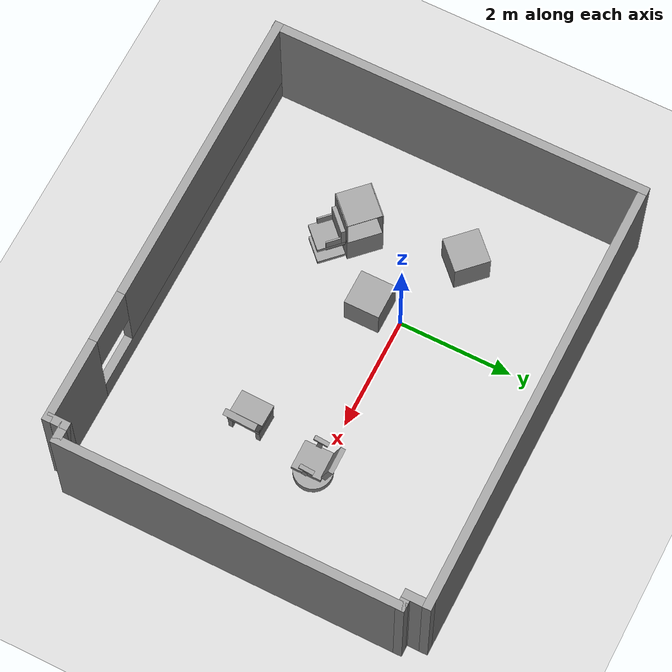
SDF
<sdf version="1.7">
 <world name="default">
  <physics name="normal" type="ode">
   <real_time_update_rate>1000</real_time_update_rate>
   <max_step_size>0.001</max_step_size>
  </physics>
  <light name="sun" type="directional">
   <pose>0 0 10 0 -0 0</pose>
   <diffuse>0.8 0.8 0.8 1</diffuse>
   <specular>0.2 0.2 0.2 1</specular>
   <attenuation>
    <range>1000</range>
    <constant>0.9</constant>
    <linear>0.01</linear>
    <quadratic>0.001</quadratic>
   </attenuation>
   <direction>-0.5 0.1 -0.9</direction>
   <spot><inner_angle>0</inner_angle><outer_angle>0</outer_angle><falloff>0</falloff></spot>
  </light>
  <model name="ground_plane">
   <static>1</static>
   <link name="link">
    <collision name="collision">
     <geometry><plane><normal>0 0 1</normal><size>100 100</size></plane></geometry>
     <surface>
      <contact><collide_bitmask>65535</collide_bitmask></contact>
      <friction><ode><mu>100</mu><mu2>50</mu2></ode></friction>
     </surface>
    </collision>
    <visual name="visual">
     <cast_shadows>0</cast_shadows>
     <geometry><plane><normal>0 0 1</normal><size>100 100</size></plane></geometry>
     <material>
      <script><uri>file://media/materials/scripts/gazebo.material</uri><name>Gazebo/Grey</name></script>
     </material>
    </visual>
   </link>
  </model>
  <gravity>0 0 -9.8</gravity>
  <magnetic_field>6e-06 2.3e-05 -4.2e-05</magnetic_field>
  <atmosphere type="adiabatic"/>
  <physics type="ode">
   <max_step_size>0.001</max_step_size>
   <real_time_factor>1</real_time_factor>
   <real_time_update_rate>1000</real_time_update_rate>
  </physics>
  <scene><ambient>0.4 0.4 0.4 1</ambient><background>0.7 0.7 0.7 1</background><shadows>1</shadows></scene>
  <spherical_coordinates>
   <surface_model>EARTH_WGS84</surface_model>
   <latitude_deg>0</latitude_deg>
   <longitude_deg>0</longitude_deg>
   <elevation>0</elevation>
   <heading_deg>0</heading_deg>
  </spherical_coordinates>
  <model name="room_model">
   <pose>0.214717 -0.451308 0 0 -0 3.14159</pose>
   <link name="Wall_53">
    <pose>-0.681 3.259 0 0 -0 0</pose>
    <visual name="Wall_53_Visual_0">
     <pose>-3.1365 0 1.1235 0 -0 0</pose>
     <geometry><box><size>1.499 0.15 2.247</size></box></geometry>
     <material>
      <script><uri>file://media/materials/scripts/gazebo.material</uri><name>Gazebo/Grey</name></script>
      <ambient>1 1 1 1</ambient>
     </material>
     <meta><layer>0</layer></meta>
    </visual>
    <collision name="Wall_53_Collision_0">
     <geometry><box><size>1.499 0.15 2.247</size></box></geometry>
     <pose>-3.1365 0 1.1235 0 -0 0</pose>
    </collision>
    <visual name="Wall_53_Visual_1">
     <pose>0.7495 0 0.25 0 -0 0</pose>
     <geometry><box><size>6.273 0.15 0.5</size></box></geometry>
     <material>
      <script><uri>file://media/materials/scripts/gazebo.material</uri><name>Gazebo/Grey</name></script>
      <ambient>1 1 1 1</ambient>
     </material>
     <meta><layer>0</layer></meta>
    </visual>
    <collision name="Wall_53_Collision_1">
     <geometry><box><size>6.273 0.15 0.5</size></box></geometry>
     <pose>0.7495 0 0.25 0 -0 0</pose>
    </collision>
    <visual name="Wall_53_Visual_2">
     <pose>1.1995 0 1.3735 0 -0 0</pose>
     <geometry><box><size>5.373 0.15 1.747</size></box></geometry>
     <material>
      <script><uri>file://media/materials/scripts/gazebo.material</uri><name>Gazebo/Grey</name></script>
      <ambient>1 1 1 1</ambient>
     </material>
     <meta><layer>0</layer></meta>
    </visual>
    <collision name="Wall_53_Collision_2">
     <geometry><box><size>5.373 0.15 1.747</size></box></geometry>
     <pose>1.1995 0 1.3735 0 -0 0</pose>
    </collision>
    <visual name="Wall_53_Visual_3">
     <pose>-1.937 0 1.7735 0 -0 0</pose>
     <geometry><box><size>0.9 0.15 0.947</size></box></geometry>
     <material>
      <script><uri>file://media/materials/scripts/gazebo.material</uri><name>Gazebo/Grey</name></script>
      <ambient>1 1 1 1</ambient>
     </material>
     <meta><layer>0</layer></meta>
    </visual>
    <collision name="Wall_53_Collision_3">
     <geometry><box><size>0.9 0.15 0.947</size></box></geometry>
     <pose>-1.937 0 1.7735 0 -0 0</pose>
    </collision>
   </link>
   <link name="Wall_59">
    <collision name="Wall_59_Collision">
     <geometry><box><size>7.835 0.15 2.247</size></box></geometry>
     <pose>0 0 1.1235 0 -0 0</pose>
    </collision>
    <visual name="Wall_59_Visual">
     <pose>0 0 1.1235 0 -0 0</pose>
     <geometry><box><size>7.835 0.15 2.247</size></box></geometry>
     <material>
      <script><uri>file://media/materials/scripts/gazebo.material</uri><name>Gazebo/Grey</name></script>
      <ambient>1 1 1 1</ambient>
     </material>
     <meta><layer>0</layer></meta>
    </visual>
    <pose>-0.7125 -3.265 0 0 -0 3.14159</pose>
   </link>
   <link name="Wall_61">
    <collision name="Wall_61_Collision">
     <geometry><box><size>0.5 0.15 2.247</size></box></geometry>
     <pose>0 0 1.1235 0 -0 0</pose>
    </collision>
    <visual name="Wall_61_Visual">
     <pose>0 0 1.1235 0 -0 0</pose>
     <geometry><box><size>0.5 0.15 2.247</size></box></geometry>
     <material>
      <script><uri>file://media/materials/scripts/gazebo.material</uri><name>Gazebo/Grey</name></script>
      <ambient>1 1 1 1</ambient>
     </material>
     <meta><layer>0</layer></meta>
    </visual>
    <pose>-4.555 -3.09 0 0 -0 1.5708</pose>
   </link>
   <link name="Wall_63">
    <collision name="Wall_63_Collision">
     <geometry><box><size>0.352 0.15 2.247</size></box></geometry>
     <pose>0 0 1.1235 0 -0 0</pose>
    </collision>
    <visual name="Wall_63_Visual">
     <pose>0 0 1.1235 0 -0 0</pose>
     <geometry><box><size>0.352 0.15 2.247</size></box></geometry>
     <material>
      <script><uri>file://media/materials/scripts/gazebo.material</uri><name>Gazebo/Grey</name></script>
      <ambient>1 1 1 1</ambient>
     </material>
     <meta><layer>0</layer></meta>
    </visual>
    <pose>-4.656 -2.915 0 0 -0 3.14159</pose>
   </link>
   <link name="Wall_68">
    <collision name="Wall_68_Collision">
     <geometry><box><size>6.032 0.15 2.247</size></box></geometry>
     <pose>0 0 1.1235 0 -0 0</pose>
    </collision>
    <visual name="Wall_68_Visual">
     <pose>0 0 1.1235 0 -0 0</pose>
     <geometry><box><size>6.032 0.15 2.247</size></box></geometry>
     <material>
      <script><uri>file://media/materials/scripts/gazebo.material</uri><name>Gazebo/Grey</name></script>
      <ambient>1 1 1 1</ambient>
     </material>
     <meta><layer>0</layer></meta>
    </visual>
    <pose>-4.757 0.026 0 0 -0 1.5708</pose>
   </link>
   <link name="Wall_70">
    <collision name="Wall_70_Collision">
     <geometry><box><size>0.416 0.15 2.247</size></box></geometry>
     <pose>0 0 1.1235 0 -0 0</pose>
    </collision>
    <visual name="Wall_70_Visual">
     <pose>0 0 1.1235 0 -0 0</pose>
     <geometry><box><size>0.416 0.15 2.247</size></box></geometry>
     <material>
      <script><uri>file://media/materials/scripts/gazebo.material</uri><name>Gazebo/Grey</name></script>
      <ambient>1 1 1 1</ambient>
     </material>
     <meta><layer>0</layer></meta>
    </visual>
    <pose>-4.624 2.967 0 0 -0 0</pose>
   </link>
   <link name="Wall_71">
    <collision name="Wall_71_Collision">
     <geometry><box><size>0.397 0.15 2.247</size></box></geometry>
     <pose>0 0 1.1235 0 -0 0</pose>
    </collision>
    <visual name="Wall_71_Visual">
     <pose>0 0 1.1235 0 -0 0</pose>
     <geometry><box><size>0.397 0.15 2.247</size></box></geometry>
     <material>
      <script><uri>file://media/materials/scripts/gazebo.material</uri><name>Gazebo/Grey</name></script>
      <ambient>1 1 1 1</ambient>
     </material>
     <meta><layer>0</layer></meta>
    </visual>
    <pose>-4.491 3.0905 0 0 -0 1.5708</pose>
   </link>
   <link name="Wall_75">
    <collision name="Wall_75_Collision">
     <geometry><box><size>6.68 0.15 2.247</size></box></geometry>
     <pose>0 0 1.1235 0 -0 0</pose>
    </collision>
    <visual name="Wall_75_Visual">
     <pose>0 0 1.1235 0 -0 0</pose>
     <geometry><box><size>6.68 0.15 2.247</size></box></geometry>
     <material>
      <script><uri>file://media/materials/scripts/gazebo.material</uri><name>Gazebo/Grey</name></script>
      <ambient>1 1 1 1</ambient>
     </material>
     <meta><layer>0</layer></meta>
    </visual>
    <pose>3.13 0 0 0 -0 1.5708</pose>
   </link>
   <static>1</static>
  </model>
  <model name="0.6223_cube">
   <link name="link">
    <inertial>
     <mass>1</mass>
     <inertia>
      <ixx>0.166667</ixx>
      <ixy>0</ixy>
      <ixz>0</ixz>
      <iyy>0.166667</iyy>
      <iyz>0</iyz>
      <izz>0.166667</izz>
     </inertia>
    </inertial>
    <visual name="visual">
     <geometry><box><size>0.6223 0.6223 0.6223</size></box></geometry>
     <material>
      <script><name>Gazebo/Grey</name><uri>file://media/materials/scripts/gazebo.material</uri></script>
      <shader type="pixel"><normal_map>__default__</normal_map></shader>
      <ambient>0.3 0.3 0.3 1</ambient>
      <diffuse>0.7 0.7 0.7 1</diffuse>
      <specular>0.01 0.01 0.01 1</specular>
      <emissive>0 0 0 1</emissive>
     </material>
    </visual>
    <collision name="collision">
     <geometry><box><size>0.6223 0.6223 0.6223</size></box></geometry>
     <surface>
      <friction>
       <ode><mu>1</mu><mu2>1</mu2><fdir1>0 0 0</fdir1><slip1>0</slip1><slip2>0</slip2></ode>
       <torsional>
        <coefficient>1</coefficient>
        <patch_radius>0</patch_radius>
        <surface_radius>0</surface_radius>
        <use_patch_radius>1</use_patch_radius>
        <ode><slip>0</slip></ode>
       </torsional>
      </friction>
      <bounce><restitution_coefficient>0</restitution_coefficient><threshold>1e+06</threshold></bounce>
      <contact>
       <collide_without_contact>0</collide_without_contact>
       <collide_without_contact_bitmask>1</collide_without_contact_bitmask>
       <collide_bitmask>1</collide_bitmask>
       <ode>
        <soft_cfm>0</soft_cfm>
        <soft_erp>0.2</soft_erp>
        <kp>1e+13</kp>
        <kd>1</kd>
        <max_vel>0.01</max_vel>
        <min_depth>0</min_depth>
       </ode>
       <bullet>
        <split_impulse>1</split_impulse>
        <split_impulse_penetration_threshold>-0.01</split_impulse_penetration_threshold>
        <soft_cfm>0</soft_cfm>
        <soft_erp>0.2</soft_erp>
        <kp>1e+13</kp>
        <kd>1</kd>
       </bullet>
      </contact>
     </surface>
    </collision>
   </link>
   <static>0</static>
   <pose>0.000692 -0.556433 0.31115 0 -0 0</pose>
  </model>
  <model name="blue_roll_chair">
   <link name="link_1">
    <inertial>
     <mass>0.217639</mass>
     <inertia>
      <ixx>0.0144615</ixx>
      <ixy>0</ixy>
      <ixz>0</ixz>
      <iyy>0.0144615</iyy>
      <iyz>0</iyz>
      <izz>0.0272049</izz>
     </inertia>
    </inertial>
    <pose>0.08152 0 -0.528447 0 -0 0</pose>
    <visual name="visual">
     <geometry><cylinder><radius>0.3302</radius><length>0.14605</length></cylinder></geometry>
     <material>
      <lighting>1</lighting>
      <script><uri>file://media/materials/scripts/gazebo.material</uri><name>Gazebo/Grey</name></script>
      <shader type="pixel"><normal_map>__default__</normal_map></shader>
      <ambient>0.3 0.3 0.3 1</ambient>
      <diffuse>0.7 0.7 0.7 1</diffuse>
      <specular>0.01 0.01 0.01 1</specular>
      <emissive>0 0 0 1</emissive>
     </material>
    </visual>
    <collision name="collision">
     <geometry><cylinder><radius>0.3302</radius><length>0.14605</length></cylinder></geometry>
     <surface>
      <friction>
       <ode><mu>1</mu><mu2>1</mu2><fdir1>0 0 0</fdir1><slip1>0</slip1><slip2>0</slip2></ode>
       <torsional>
        <coefficient>1</coefficient>
        <patch_radius>0</patch_radius>
        <surface_radius>0</surface_radius>
        <use_patch_radius>1</use_patch_radius>
        <ode><slip>0</slip></ode>
       </torsional>
      </friction>
      <bounce><restitution_coefficient>0</restitution_coefficient><threshold>1e+06</threshold></bounce>
      <contact>
       <collide_without_contact>0</collide_without_contact>
       <collide_without_contact_bitmask>1</collide_without_contact_bitmask>
       <collide_bitmask>1</collide_bitmask>
       <ode>
        <soft_cfm>0</soft_cfm>
        <soft_erp>0.2</soft_erp>
        <kp>1e+13</kp>
        <kd>1</kd>
        <max_vel>0.01</max_vel>
        <min_depth>0</min_depth>
       </ode>
       <bullet>
        <split_impulse>1</split_impulse>
        <split_impulse_penetration_threshold>-0.01</split_impulse_penetration_threshold>
        <soft_cfm>0</soft_cfm>
        <soft_erp>0.2</soft_erp>
        <kp>1e+13</kp>
        <kd>1</kd>
       </bullet>
      </contact>
     </surface>
    </collision>
   </link>
   <link name="link_2">
    <inertial>
     <mass>0.148275</mass>
     <inertia>
      <ixx>0.00571396</ixx>
      <ixy>0</ixy>
      <ixz>0</ixz>
      <iyy>0.00571396</iyy>
      <iyz>0</iyz>
      <izz>0.00043048</izz>
     </inertia>
    </inertial>
    <pose>0.08152 0 -0.334772 0 -0 0</pose>
    <visual name="visual">
     <geometry><cylinder><radius>0.0762</radius><length>0.5334</length></cylinder></geometry>
     <material>
      <lighting>1</lighting>
      <script><uri>file://media/materials/scripts/gazebo.material</uri><name>Gazebo/Grey</name></script>
      <shader type="pixel"><normal_map>__default__</normal_map></shader>
      <ambient>0.3 0.3 0.3 1</ambient>
      <diffuse>0.7 0.7 0.7 1</diffuse>
      <specular>0.01 0.01 0.01 1</specular>
      <emissive>0 0 0 1</emissive>
     </material>
    </visual>
    <collision name="collision">
     <geometry><cylinder><radius>0.0762</radius><length>0.5334</length></cylinder></geometry>
     <surface>
      <friction>
       <ode><mu>1</mu><mu2>1</mu2><fdir1>0 0 0</fdir1><slip1>0</slip1><slip2>0</slip2></ode>
       <torsional>
        <coefficient>1</coefficient>
        <patch_radius>0</patch_radius>
        <surface_radius>0</surface_radius>
        <use_patch_radius>1</use_patch_radius>
        <ode><slip>0</slip></ode>
       </torsional>
      </friction>
      <bounce><restitution_coefficient>0</restitution_coefficient><threshold>1e+06</threshold></bounce>
      <contact>
       <collide_without_contact>0</collide_without_contact>
       <collide_without_contact_bitmask>1</collide_without_contact_bitmask>
       <collide_bitmask>1</collide_bitmask>
       <ode>
        <soft_cfm>0</soft_cfm>
        <soft_erp>0.2</soft_erp>
        <kp>1e+13</kp>
        <kd>1</kd>
        <max_vel>0.01</max_vel>
        <min_depth>0</min_depth>
       </ode>
       <bullet>
        <split_impulse>1</split_impulse>
        <split_impulse_penetration_threshold>-0.01</split_impulse_penetration_threshold>
        <soft_cfm>0</soft_cfm>
        <soft_erp>0.2</soft_erp>
        <kp>1e+13</kp>
        <kd>1</kd>
       </bullet>
      </contact>
     </surface>
    </collision>
   </link>
   <link name="link_3">
    <inertial>
     <mass>0.764476</mass>
     <inertia>
      <ixx>0.100938</ixx>
      <ixy>0</ixy>
      <ixz>0</ixz>
      <iyy>0.127413</iyy>
      <iyz>0</iyz>
      <izz>0.100938</izz>
     </inertia>
    </inertial>
    <pose>0.08152 0 -0.063372 0 -0 0</pose>
    <visual name="visual">
     <geometry><box><size>0.5207 0.508 0.0762</size></box></geometry>
     <material>
      <lighting>1</lighting>
      <script><uri>file://media/materials/scripts/gazebo.material</uri><name>Gazebo/Grey</name></script>
      <shader type="pixel"><normal_map>__default__</normal_map></shader>
      <ambient>0.3 0.3 0.3 1</ambient>
      <diffuse>0.7 0.7 0.7 1</diffuse>
      <specular>0.01 0.01 0.01 1</specular>
      <emissive>0 0 0 1</emissive>
     </material>
    </visual>
    <collision name="collision">
     <geometry><box><size>0.5207 0.508 0.0762</size></box></geometry>
     <surface>
      <friction>
       <ode><mu>1</mu><mu2>1</mu2><fdir1>0 0 0</fdir1><slip1>0</slip1><slip2>0</slip2></ode>
       <torsional>
        <coefficient>1</coefficient>
        <patch_radius>0</patch_radius>
        <surface_radius>0</surface_radius>
        <use_patch_radius>1</use_patch_radius>
        <ode><slip>0</slip></ode>
       </torsional>
      </friction>
      <bounce><restitution_coefficient>0</restitution_coefficient><threshold>1e+06</threshold></bounce>
      <contact>
       <collide_without_contact>0</collide_without_contact>
       <collide_without_contact_bitmask>1</collide_without_contact_bitmask>
       <collide_bitmask>1</collide_bitmask>
       <ode>
        <soft_cfm>0</soft_cfm>
        <soft_erp>0.2</soft_erp>
        <kp>1e+13</kp>
        <kd>1</kd>
        <max_vel>0.01</max_vel>
        <min_depth>0</min_depth>
       </ode>
       <bullet>
        <split_impulse>1</split_impulse>
        <split_impulse_penetration_threshold>-0.01</split_impulse_penetration_threshold>
        <soft_cfm>0</soft_cfm>
        <soft_erp>0.2</soft_erp>
        <kp>1e+13</kp>
        <kd>1</kd>
       </bullet>
      </contact>
     </surface>
    </collision>
   </link>
   <link name="link_5_clone">
    <inertial>
     <mass>0.0575704</mass>
     <inertia>
      <ixx>0.00481343</ixx>
      <ixy>0</ixy>
      <ixz>0</ixz>
      <iyy>0.00959506</iyy>
      <iyz>0</iyz>
      <izz>0.00481343</izz>
     </inertia>
    </inertial>
    <pose>0.08152 0.254 0.073742 0 -0.15708 0</pose>
    <visual name="visual">
     <geometry><box><size>0.0889 0.0381 0.2794</size></box></geometry>
     <material>
      <lighting>1</lighting>
      <script><uri>file://media/materials/scripts/gazebo.material</uri><name>Gazebo/Grey</name></script>
      <shader type="pixel"><normal_map>__default__</normal_map></shader>
      <ambient>0.3 0.3 0.3 1</ambient>
      <diffuse>0.7 0.7 0.7 1</diffuse>
      <specular>0.01 0.01 0.01 1</specular>
      <emissive>0 0 0 1</emissive>
     </material>
    </visual>
    <collision name="collision">
     <geometry><box><size>0.0889 0.0381 0.2794</size></box></geometry>
     <surface>
      <friction>
       <ode><mu>1</mu><mu2>1</mu2><fdir1>0 0 0</fdir1><slip1>0</slip1><slip2>0</slip2></ode>
       <torsional>
        <coefficient>1</coefficient>
        <patch_radius>0</patch_radius>
        <surface_radius>0</surface_radius>
        <use_patch_radius>1</use_patch_radius>
        <ode><slip>0</slip></ode>
       </torsional>
      </friction>
      <bounce><restitution_coefficient>0</restitution_coefficient><threshold>1e+06</threshold></bounce>
      <contact>
       <collide_without_contact>0</collide_without_contact>
       <collide_without_contact_bitmask>1</collide_without_contact_bitmask>
       <collide_bitmask>1</collide_bitmask>
       <ode>
        <soft_cfm>0</soft_cfm>
        <soft_erp>0.2</soft_erp>
        <kp>1e+13</kp>
        <kd>1</kd>
        <max_vel>0.01</max_vel>
        <min_depth>0</min_depth>
       </ode>
       <bullet>
        <split_impulse>1</split_impulse>
        <split_impulse_penetration_threshold>-0.01</split_impulse_penetration_threshold>
        <soft_cfm>0</soft_cfm>
        <soft_erp>0.2</soft_erp>
        <kp>1e+13</kp>
        <kd>1</kd>
       </bullet>
      </contact>
     </surface>
    </collision>
   </link>
   <link name="link_5_clone_clone">
    <inertial>
     <mass>0.0575704</mass>
     <inertia>
      <ixx>0.00481343</ixx>
      <ixy>0</ixy>
      <ixz>0</ixz>
      <iyy>0.00959506</iyy>
      <iyz>0</iyz>
      <izz>0.00481343</izz>
     </inertia>
    </inertial>
    <pose>0.078087 -0.254 0.073742 0 -0.15708 0</pose>
    <visual name="visual">
     <geometry><box><size>0.0889 0.0381 0.2794</size></box></geometry>
     <material>
      <lighting>1</lighting>
      <script><uri>file://media/materials/scripts/gazebo.material</uri><name>Gazebo/Grey</name></script>
      <shader type="pixel"><normal_map>__default__</normal_map></shader>
      <ambient>0.3 0.3 0.3 1</ambient>
      <diffuse>0.7 0.7 0.7 1</diffuse>
      <specular>0.01 0.01 0.01 1</specular>
      <emissive>0 0 0 1</emissive>
     </material>
    </visual>
    <collision name="collision">
     <geometry><box><size>0.0889 0.0381 0.2794</size></box></geometry>
     <surface>
      <friction>
       <ode><mu>1</mu><mu2>1</mu2><fdir1>0 0 0</fdir1><slip1>0</slip1><slip2>0</slip2></ode>
       <torsional>
        <coefficient>1</coefficient>
        <patch_radius>0</patch_radius>
        <surface_radius>0</surface_radius>
        <use_patch_radius>1</use_patch_radius>
        <ode><slip>0</slip></ode>
       </torsional>
      </friction>
      <bounce><restitution_coefficient>0</restitution_coefficient><threshold>1e+06</threshold></bounce>
      <contact>
       <collide_without_contact>0</collide_without_contact>
       <collide_without_contact_bitmask>1</collide_without_contact_bitmask>
       <collide_bitmask>1</collide_bitmask>
       <ode>
        <soft_cfm>0</soft_cfm>
        <soft_erp>0.2</soft_erp>
        <kp>1e+13</kp>
        <kd>1</kd>
        <max_vel>0.01</max_vel>
        <min_depth>0</min_depth>
       </ode>
       <bullet>
        <split_impulse>1</split_impulse>
        <split_impulse_penetration_threshold>-0.01</split_impulse_penetration_threshold>
        <soft_cfm>0</soft_cfm>
        <soft_erp>0.2</soft_erp>
        <kp>1e+13</kp>
        <kd>1</kd>
       </bullet>
      </contact>
     </surface>
    </collision>
   </link>
   <link name="link_6_clone">
    <inertial>
     <mass>0.120511</mass>
     <inertia>
      <ixx>0.0101882</ixx>
      <ixy>0</ixy>
      <ixz>0</ixz>
      <iyy>0.0200851</iyy>
      <iyz>0</iyz>
      <izz>0.0101882</izz>
     </inertia>
    </inertial>
    <pose>0.05612 0.26494 0.202779 0 -0.226893 0</pose>
    <visual name="visual">
     <geometry><box><size>0.254 0.0762 0.047625</size></box></geometry>
     <material>
      <lighting>1</lighting>
      <script><uri>file://media/materials/scripts/gazebo.material</uri><name>Gazebo/Grey</name></script>
      <shader type="pixel"><normal_map>__default__</normal_map></shader>
      <ambient>0.3 0.3 0.3 1</ambient>
      <diffuse>0.7 0.7 0.7 1</diffuse>
      <specular>0.01 0.01 0.01 1</specular>
      <emissive>0 0 0 1</emissive>
     </material>
    </visual>
    <collision name="collision">
     <geometry><box><size>0.254 0.0762 0.047625</size></box></geometry>
     <surface>
      <friction>
       <ode><mu>1</mu><mu2>1</mu2><fdir1>0 0 0</fdir1><slip1>0</slip1><slip2>0</slip2></ode>
       <torsional>
        <coefficient>1</coefficient>
        <patch_radius>0</patch_radius>
        <surface_radius>0</surface_radius>
        <use_patch_radius>1</use_patch_radius>
        <ode><slip>0</slip></ode>
       </torsional>
      </friction>
      <bounce><restitution_coefficient>0</restitution_coefficient><threshold>1e+06</threshold></bounce>
      <contact>
       <collide_without_contact>0</collide_without_contact>
       <collide_without_contact_bitmask>1</collide_without_contact_bitmask>
       <collide_bitmask>1</collide_bitmask>
       <ode>
        <soft_cfm>0</soft_cfm>
        <soft_erp>0.2</soft_erp>
        <kp>1e+13</kp>
        <kd>1</kd>
        <max_vel>0.01</max_vel>
        <min_depth>0</min_depth>
       </ode>
       <bullet>
        <split_impulse>1</split_impulse>
        <split_impulse_penetration_threshold>-0.01</split_impulse_penetration_threshold>
        <soft_cfm>0</soft_cfm>
        <soft_erp>0.2</soft_erp>
        <kp>1e+13</kp>
        <kd>1</kd>
       </bullet>
      </contact>
     </surface>
    </collision>
   </link>
   <link name="link_6_clone_clone">
    <inertial>
     <mass>0.120511</mass>
     <inertia>
      <ixx>0.0101882</ixx>
      <ixy>0</ixy>
      <ixz>0</ixz>
      <iyy>0.0200851</iyy>
      <iyz>0</iyz>
      <izz>0.0101882</izz>
     </inertia>
    </inertial>
    <pose>0.05612 -0.26494 0.213442 0 -0.226893 0</pose>
    <visual name="visual">
     <geometry><box><size>0.254 0.0762 0.047625</size></box></geometry>
     <material>
      <lighting>1</lighting>
      <script><uri>file://media/materials/scripts/gazebo.material</uri><name>Gazebo/Grey</name></script>
      <shader type="pixel"><normal_map>__default__</normal_map></shader>
      <ambient>0.3 0.3 0.3 1</ambient>
      <diffuse>0.7 0.7 0.7 1</diffuse>
      <specular>0.01 0.01 0.01 1</specular>
      <emissive>0 0 0 1</emissive>
     </material>
    </visual>
    <collision name="collision">
     <geometry><box><size>0.254 0.0762 0.047625</size></box></geometry>
     <surface>
      <friction>
       <ode><mu>1</mu><mu2>1</mu2><fdir1>0 0 0</fdir1><slip1>0</slip1><slip2>0</slip2></ode>
       <torsional>
        <coefficient>1</coefficient>
        <patch_radius>0</patch_radius>
        <surface_radius>0</surface_radius>
        <use_patch_radius>1</use_patch_radius>
        <ode><slip>0</slip></ode>
       </torsional>
      </friction>
      <bounce><restitution_coefficient>0</restitution_coefficient><threshold>1e+06</threshold></bounce>
      <contact>
       <collide_without_contact>0</collide_without_contact>
       <collide_without_contact_bitmask>1</collide_without_contact_bitmask>
       <collide_bitmask>1</collide_bitmask>
       <ode>
        <soft_cfm>0</soft_cfm>
        <soft_erp>0.2</soft_erp>
        <kp>1e+13</kp>
        <kd>1</kd>
        <max_vel>0.01</max_vel>
        <min_depth>0</min_depth>
       </ode>
       <bullet>
        <split_impulse>1</split_impulse>
        <split_impulse_penetration_threshold>-0.01</split_impulse_penetration_threshold>
        <soft_cfm>0</soft_cfm>
        <soft_erp>0.2</soft_erp>
        <kp>1e+13</kp>
        <kd>1</kd>
       </bullet>
      </contact>
     </surface>
    </collision>
   </link>
   <link name="link_8">
    <inertial>
     <mass>0.748762</mass>
     <inertia>
      <ixx>0.0973797</ixx>
      <ixy>0</ixy>
      <ixz>0</ixz>
      <iyy>0.0973797</iyy>
      <iyz>0</iyz>
      <izz>0.124794</izz>
     </inertia>
    </inertial>
    <pose>-0.23598 0 0.127128 0 -0.270526 0</pose>
    <visual name="visual">
     <geometry><box><size>0.00635 0.05715 0.381</size></box></geometry>
     <material>
      <lighting>1</lighting>
      <script><uri>file://media/materials/scripts/gazebo.material</uri><name>Gazebo/Grey</name></script>
      <shader type="pixel"><normal_map>__default__</normal_map></shader>
      <ambient>0.3 0.3 0.3 1</ambient>
      <diffuse>0.7 0.7 0.7 1</diffuse>
      <specular>0.01 0.01 0.01 1</specular>
      <emissive>0 0 0 1</emissive>
     </material>
    </visual>
    <collision name="collision">
     <geometry><box><size>0.00635 0.05715 0.381</size></box></geometry>
     <surface>
      <friction>
       <ode><mu>1</mu><mu2>1</mu2><fdir1>0 0 0</fdir1><slip1>0</slip1><slip2>0</slip2></ode>
       <torsional>
        <coefficient>1</coefficient>
        <patch_radius>0</patch_radius>
        <surface_radius>0</surface_radius>
        <use_patch_radius>1</use_patch_radius>
        <ode><slip>0</slip></ode>
       </torsional>
      </friction>
      <bounce><restitution_coefficient>0</restitution_coefficient><threshold>1e+06</threshold></bounce>
      <contact>
       <collide_without_contact>0</collide_without_contact>
       <collide_without_contact_bitmask>1</collide_without_contact_bitmask>
       <collide_bitmask>1</collide_bitmask>
       <ode>
        <soft_cfm>0</soft_cfm>
        <soft_erp>0.2</soft_erp>
        <kp>1e+13</kp>
        <kd>1</kd>
        <max_vel>0.01</max_vel>
        <min_depth>0</min_depth>
       </ode>
       <bullet>
        <split_impulse>1</split_impulse>
        <split_impulse_penetration_threshold>-0.01</split_impulse_penetration_threshold>
        <soft_cfm>0</soft_cfm>
        <soft_erp>0.2</soft_erp>
        <kp>1e+13</kp>
        <kd>1</kd>
       </bullet>
      </contact>
     </surface>
    </collision>
   </link>
   <link name="link_9">
    <inertial>
     <mass>0.182933</mass>
     <inertia>
      <ixx>0.0304888</ixx>
      <ixy>0</ixy>
      <ixz>0</ixz>
      <iyy>0.0157545</iyy>
      <iyz>0</iyz>
      <izz>0.0157545</izz>
     </inertia>
    </inertial>
    <pose>-0.28043 0 0.235757 0 -0.296706 0</pose>
    <visual name="visual">
     <geometry><box><size>0.085725 0.4572 0.4572</size></box></geometry>
     <material>
      <lighting>1</lighting>
      <script><uri>file://media/materials/scripts/gazebo.material</uri><name>Gazebo/Grey</name></script>
      <shader type="pixel"><normal_map>__default__</normal_map></shader>
      <ambient>0.3 0.3 0.3 1</ambient>
      <diffuse>0.7 0.7 0.7 1</diffuse>
      <specular>0.01 0.01 0.01 1</specular>
      <emissive>0 0 0 1</emissive>
     </material>
    </visual>
    <collision name="collision">
     <geometry><box><size>0.085725 0.4572 0.4572</size></box></geometry>
     <surface>
      <friction>
       <ode><mu>1</mu><mu2>1</mu2><fdir1>0 0 0</fdir1><slip1>0</slip1><slip2>0</slip2></ode>
       <torsional>
        <coefficient>1</coefficient>
        <patch_radius>0</patch_radius>
        <surface_radius>0</surface_radius>
        <use_patch_radius>1</use_patch_radius>
        <ode><slip>0</slip></ode>
       </torsional>
      </friction>
      <bounce><restitution_coefficient>0</restitution_coefficient><threshold>1e+06</threshold></bounce>
      <contact>
       <collide_without_contact>0</collide_without_contact>
       <collide_without_contact_bitmask>1</collide_without_contact_bitmask>
       <collide_bitmask>1</collide_bitmask>
       <ode>
        <soft_cfm>0</soft_cfm>
        <soft_erp>0.2</soft_erp>
        <kp>1e+13</kp>
        <kd>1</kd>
        <max_vel>0.01</max_vel>
        <min_depth>0</min_depth>
       </ode>
       <bullet>
        <split_impulse>1</split_impulse>
        <split_impulse_penetration_threshold>-0.01</split_impulse_penetration_threshold>
        <soft_cfm>0</soft_cfm>
        <soft_erp>0.2</soft_erp>
        <kp>1e+13</kp>
        <kd>1</kd>
       </bullet>
      </contact>
     </surface>
    </collision>
   </link>
   <joint name="link_2_JOINT_1" type="fixed">
    <parent>link_2</parent>
    <child>link_1</child>
    <physics>
     <ode><limit><cfm>0</cfm><erp>0.2</erp></limit><suspension><cfm>0</cfm><erp>0.2</erp></suspension></ode>
    </physics>
   </joint>
   <joint name="link_3_JOINT_0" type="fixed">
    <parent>link_3</parent>
    <child>link_2</child>
    <physics>
     <ode><limit><cfm>0</cfm><erp>0.2</erp></limit><suspension><cfm>0</cfm><erp>0.2</erp></suspension></ode>
    </physics>
   </joint>
   <joint name="link_3_JOINT_2" type="fixed">
    <parent>link_3</parent>
    <child>link_5_clone_clone</child>
    <physics>
     <ode><limit><cfm>0</cfm><erp>0.2</erp></limit><suspension><cfm>0</cfm><erp>0.2</erp></suspension></ode>
    </physics>
   </joint>
   <joint name="link_3_JOINT_3" type="fixed">
    <parent>link_3</parent>
    <child>link_5_clone</child>
    <physics>
     <ode><limit><cfm>0</cfm><erp>0.2</erp></limit><suspension><cfm>0</cfm><erp>0.2</erp></suspension></ode>
    </physics>
   </joint>
   <joint name="link_3_JOINT_6" type="fixed">
    <parent>link_3</parent>
    <child>link_8</child>
    <physics>
     <ode><limit><cfm>0</cfm><erp>0.2</erp></limit><suspension><cfm>0</cfm><erp>0.2</erp></suspension></ode>
    </physics>
   </joint>
   <joint name="link_3_JOINT_7" type="fixed">
    <parent>link_3</parent>
    <child>link_9</child>
    <physics>
     <ode><limit><cfm>0</cfm><erp>0.2</erp></limit><suspension><cfm>0</cfm><erp>0.2</erp></suspension></ode>
    </physics>
   </joint>
   <joint name="link_5_clone_JOINT_4" type="fixed">
    <parent>link_5_clone</parent>
    <child>link_6_clone</child>
    <physics>
     <ode><limit><cfm>0</cfm><erp>0.2</erp></limit><suspension><cfm>0</cfm><erp>0.2</erp></suspension></ode>
    </physics>
   </joint>
   <joint name="link_5_clone_clone_JOINT_5" type="fixed">
    <parent>link_5_clone_clone</parent>
    <child>link_6_clone_clone</child>
    <physics>
     <ode><limit><cfm>0</cfm><erp>0.2</erp></limit><suspension><cfm>0</cfm><erp>0.2</erp></suspension></ode>
    </physics>
   </joint>
   <static>0</static>
   <pose>2.95215 0.001786 0.601472 0 2e-06 -1.55943</pose>
  </model>
  <model name="0.6223_cube_0">
   <link name="link">
    <inertial>
     <mass>1</mass>
     <inertia>
      <ixx>0.166667</ixx>
      <ixy>0</ixy>
      <ixz>0</ixz>
      <iyy>0.166667</iyy>
      <iyz>0</iyz>
      <izz>0.166667</izz>
     </inertia>
    </inertial>
    <visual name="visual">
     <geometry><box><size>0.6223 0.6223 0.6223</size></box></geometry>
     <material>
      <script><name>Gazebo/Grey</name><uri>file://media/materials/scripts/gazebo.material</uri></script>
      <shader type="pixel"><normal_map>__default__</normal_map></shader>
      <ambient>0.3 0.3 0.3 1</ambient>
      <diffuse>0.7 0.7 0.7 1</diffuse>
      <specular>0.01 0.01 0.01 1</specular>
      <emissive>0 0 0 1</emissive>
     </material>
    </visual>
    <collision name="collision">
     <geometry><box><size>0.6223 0.6223 0.6223</size></box></geometry>
     <surface>
      <friction>
       <ode><mu>1</mu><mu2>1</mu2><fdir1>0 0 0</fdir1><slip1>0</slip1><slip2>0</slip2></ode>
       <torsional>
        <coefficient>1</coefficient>
        <patch_radius>0</patch_radius>
        <surface_radius>0</surface_radius>
        <use_patch_radius>1</use_patch_radius>
        <ode><slip>0</slip></ode>
       </torsional>
      </friction>
      <bounce><restitution_coefficient>0</restitution_coefficient><threshold>1e+06</threshold></bounce>
      <contact>
       <collide_without_contact>0</collide_without_contact>
       <collide_without_contact_bitmask>1</collide_without_contact_bitmask>
       <collide_bitmask>1</collide_bitmask>
       <ode>
        <soft_cfm>0</soft_cfm>
        <soft_erp>0.2</soft_erp>
        <kp>1e+13</kp>
        <kd>1</kd>
        <max_vel>0.01</max_vel>
        <min_depth>0</min_depth>
       </ode>
       <bullet>
        <split_impulse>1</split_impulse>
        <split_impulse_penetration_threshold>-0.01</split_impulse_penetration_threshold>
        <soft_cfm>0</soft_cfm>
        <soft_erp>0.2</soft_erp>
        <kp>1e+13</kp>
        <kd>1</kd>
       </bullet>
      </contact>
     </surface>
    </collision>
   </link>
   <static>0</static>
   <pose>-1.40869 0.495475 0.31115 0 -0 0.785397</pose>
  </model>
  <model name="gray_lean_chair">
   <link name="link_0">
    <inertial>
     <mass>0.288675</mass>
     <inertia>
      <ixx>0.119705</ixx>
      <ixy>0</ixy>
      <ixz>0</ixz>
      <iyy>0.0244605</iyy>
      <iyz>0</iyz>
      <izz>0.143357</izz>
     </inertia>
    </inertial>
    <pose>0 0.0625 0.038512 0 -0 0</pose>
    <visual name="visual">
     <geometry><box><size>0.5842 0.508 0.1143</size></box></geometry>
     <material>
      <lighting>1</lighting>
      <script><uri>file://media/materials/scripts/gazebo.material</uri><name>Gazebo/Grey</name></script>
      <shader type="pixel"><normal_map>__default__</normal_map></shader>
      <ambient>0.3 0.3 0.3 1</ambient>
      <diffuse>0.7 0.7 0.7 1</diffuse>
      <specular>0.01 0.01 0.01 1</specular>
      <emissive>0 0 0 1</emissive>
     </material>
    </visual>
    <collision name="collision">
     <geometry><box><size>0.5842 0.508 0.1143</size></box></geometry>
     <surface>
      <friction>
       <ode><mu>1</mu><mu2>1</mu2><fdir1>0 0 0</fdir1><slip1>0</slip1><slip2>0</slip2></ode>
       <torsional>
        <coefficient>1</coefficient>
        <patch_radius>0</patch_radius>
        <surface_radius>0</surface_radius>
        <use_patch_radius>1</use_patch_radius>
        <ode><slip>0</slip></ode>
       </torsional>
      </friction>
      <bounce><restitution_coefficient>0</restitution_coefficient><threshold>1e+06</threshold></bounce>
      <contact>
       <collide_without_contact>0</collide_without_contact>
       <collide_without_contact_bitmask>1</collide_without_contact_bitmask>
       <collide_bitmask>1</collide_bitmask>
       <ode>
        <soft_cfm>0</soft_cfm>
        <soft_erp>0.2</soft_erp>
        <kp>1e+13</kp>
        <kd>1</kd>
        <max_vel>0.01</max_vel>
        <min_depth>0</min_depth>
       </ode>
       <bullet>
        <split_impulse>1</split_impulse>
        <split_impulse_penetration_threshold>-0.01</split_impulse_penetration_threshold>
        <soft_cfm>0</soft_cfm>
        <soft_erp>0.2</soft_erp>
        <kp>1e+13</kp>
        <kd>1</kd>
       </bullet>
      </contact>
     </surface>
    </collision>
   </link>
   <link name="link_1">
    <inertial>
     <mass>0.0681541</mass>
     <inertia>
      <ixx>0.0073775</ixx>
      <ixy>0</ixy>
      <ixz>0</ixz>
      <iyy>0.00576774</iyy>
      <iyz>0</iyz>
      <izz>0.00178623</izz>
     </inertia>
    </inertial>
    <pose>0.25 0.0625 -0.136938 0 1.5707 0</pose>
    <visual name="visual">
     <geometry><box><size>0.457201 0.4572 0.0762</size></box></geometry>
     <material>
      <lighting>1</lighting>
      <script><uri>file://media/materials/scripts/gazebo.material</uri><name>Gazebo/Grey</name></script>
      <shader type="pixel"><normal_map>__default__</normal_map></shader>
      <ambient>0.3 0.3 0.3 1</ambient>
      <diffuse>0.7 0.7 0.7 1</diffuse>
      <specular>0.01 0.01 0.01 1</specular>
      <emissive>0 0 0 1</emissive>
     </material>
    </visual>
    <collision name="collision">
     <geometry><box><size>0.4572 0.4572 0.0762</size></box></geometry>
     <surface>
      <friction>
       <ode><mu>1</mu><mu2>1</mu2><fdir1>0 0 0</fdir1><slip1>0</slip1><slip2>0</slip2></ode>
       <torsional>
        <coefficient>1</coefficient>
        <patch_radius>0</patch_radius>
        <surface_radius>0</surface_radius>
        <use_patch_radius>1</use_patch_radius>
        <ode><slip>0</slip></ode>
       </torsional>
      </friction>
      <bounce><restitution_coefficient>0</restitution_coefficient><threshold>1e+06</threshold></bounce>
      <contact>
       <collide_without_contact>0</collide_without_contact>
       <collide_without_contact_bitmask>1</collide_without_contact_bitmask>
       <collide_bitmask>1</collide_bitmask>
       <ode>
        <soft_cfm>0</soft_cfm>
        <soft_erp>0.2</soft_erp>
        <kp>1e+13</kp>
        <kd>1</kd>
        <max_vel>0.01</max_vel>
        <min_depth>0</min_depth>
       </ode>
       <bullet>
        <split_impulse>1</split_impulse>
        <split_impulse_penetration_threshold>-0.01</split_impulse_penetration_threshold>
        <soft_cfm>0</soft_cfm>
        <soft_erp>0.2</soft_erp>
        <kp>1e+13</kp>
        <kd>1</kd>
       </bullet>
      </contact>
     </surface>
    </collision>
   </link>
   <link name="link_1_clone">
    <inertial>
     <mass>0.0681541</mass>
     <inertia>
      <ixx>0.0073775</ixx>
      <ixy>0</ixy>
      <ixz>0</ixz>
      <iyy>0.00576774</iyy>
      <iyz>0</iyz>
      <izz>0.00178623</izz>
     </inertia>
    </inertial>
    <pose>-0.25 0.0625 -0.136938 0 1.5707 0</pose>
    <visual name="visual">
     <geometry><box><size>0.457201 0.4572 0.0762</size></box></geometry>
     <material>
      <lighting>1</lighting>
      <script><uri>file://media/materials/scripts/gazebo.material</uri><name>Gazebo/Grey</name></script>
      <shader type="pixel"><normal_map>__default__</normal_map></shader>
      <ambient>0.3 0.3 0.3 1</ambient>
      <diffuse>0.7 0.7 0.7 1</diffuse>
      <specular>0.01 0.01 0.01 1</specular>
      <emissive>0 0 0 1</emissive>
     </material>
    </visual>
    <collision name="collision">
     <geometry><box><size>0.4572 0.4572 0.0762</size></box></geometry>
     <surface>
      <friction>
       <ode><mu>1</mu><mu2>1</mu2><fdir1>0 0 0</fdir1><slip1>0</slip1><slip2>0</slip2></ode>
       <torsional>
        <coefficient>1</coefficient>
        <patch_radius>0</patch_radius>
        <surface_radius>0</surface_radius>
        <use_patch_radius>1</use_patch_radius>
        <ode><slip>0</slip></ode>
       </torsional>
      </friction>
      <bounce><restitution_coefficient>0</restitution_coefficient><threshold>1e+06</threshold></bounce>
      <contact>
       <collide_without_contact>0</collide_without_contact>
       <collide_without_contact_bitmask>1</collide_without_contact_bitmask>
       <collide_bitmask>1</collide_bitmask>
       <ode>
        <soft_cfm>0</soft_cfm>
        <soft_erp>0.2</soft_erp>
        <kp>1e+13</kp>
        <kd>1</kd>
        <max_vel>0.01</max_vel>
        <min_depth>0</min_depth>
       </ode>
       <bullet>
        <split_impulse>1</split_impulse>
        <split_impulse_penetration_threshold>-0.01</split_impulse_penetration_threshold>
        <soft_cfm>0</soft_cfm>
        <soft_erp>0.2</soft_erp>
        <kp>1e+13</kp>
        <kd>1</kd>
       </bullet>
      </contact>
     </surface>
    </collision>
   </link>
   <link name="link_2">
    <inertial>
     <mass>0.0761033</mass>
     <inertia>
      <ixx>0.00637868</ixx>
      <ixy>0</ixy>
      <ixz>0</ixz>
      <iyy>0.0126839</iyy>
      <iyz>0</iyz>
      <izz>0.00637868</izz>
     </inertia>
    </inertial>
    <pose>0 -0.1875 0.235363 0.322886 -0 0</pose>
    <visual name="visual">
     <geometry><box><size>0.5842 0.1143 0.3937</size></box></geometry>
     <material>
      <lighting>1</lighting>
      <script><uri>file://media/materials/scripts/gazebo.material</uri><name>Gazebo/Grey</name></script>
      <shader type="pixel"><normal_map>__default__</normal_map></shader>
      <ambient>0.3 0.3 0.3 1</ambient>
      <diffuse>0.7 0.7 0.7 1</diffuse>
      <specular>0.01 0.01 0.01 1</specular>
      <emissive>0 0 0 1</emissive>
     </material>
    </visual>
    <collision name="collision">
     <geometry><box><size>0.5842 0.1143 0.3937</size></box></geometry>
     <surface>
      <friction>
       <ode><mu>1</mu><mu2>1</mu2><fdir1>0 0 0</fdir1><slip1>0</slip1><slip2>0</slip2></ode>
       <torsional>
        <coefficient>1</coefficient>
        <patch_radius>0</patch_radius>
        <surface_radius>0</surface_radius>
        <use_patch_radius>1</use_patch_radius>
        <ode><slip>0</slip></ode>
       </torsional>
      </friction>
      <bounce><restitution_coefficient>0</restitution_coefficient><threshold>1e+06</threshold></bounce>
      <contact>
       <collide_without_contact>0</collide_without_contact>
       <collide_without_contact_bitmask>1</collide_without_contact_bitmask>
       <collide_bitmask>1</collide_bitmask>
       <ode>
        <soft_cfm>0</soft_cfm>
        <soft_erp>0.2</soft_erp>
        <kp>1e+13</kp>
        <kd>1</kd>
        <max_vel>0.01</max_vel>
        <min_depth>0</min_depth>
       </ode>
       <bullet>
        <split_impulse>1</split_impulse>
        <split_impulse_penetration_threshold>-0.01</split_impulse_penetration_threshold>
        <soft_cfm>0</soft_cfm>
        <soft_erp>0.2</soft_erp>
        <kp>1e+13</kp>
        <kd>1</kd>
       </bullet>
      </contact>
     </surface>
    </collision>
   </link>
   <joint name="link_0_JOINT_0" type="fixed">
    <parent>link_0</parent>
    <child>link_2</child>
    <physics>
     <ode><limit><cfm>0</cfm><erp>0.2</erp></limit><suspension><cfm>0</cfm><erp>0.2</erp></suspension></ode>
    </physics>
   </joint>
   <joint name="link_0_JOINT_1" type="fixed">
    <parent>link_0</parent>
    <child>link_1</child>
    <physics>
     <ode><limit><cfm>0</cfm><erp>0.2</erp></limit><suspension><cfm>0</cfm><erp>0.2</erp></suspension></ode>
    </physics>
   </joint>
   <joint name="link_0_JOINT_2" type="fixed">
    <parent>link_0</parent>
    <child>link_1_clone</child>
    <physics>
     <ode><limit><cfm>0</cfm><erp>0.2</erp></limit><suspension><cfm>0</cfm><erp>0.2</erp></suspension></ode>
    </physics>
   </joint>
   <static>0</static>
   <pose>2.68156 -1.37329 0.365542 0 2e-06 1.54737</pose>
  </model>
  <model name="tunnel_box">
   <link name="link_0">
    <inertial>
     <mass>1</mass>
     <inertia>
      <ixx>0.166667</ixx>
      <ixy>0</ixy>
      <ixz>0</ixz>
      <iyy>0.166667</iyy>
      <iyz>0</iyz>
      <izz>0.166667</izz>
     </inertia>
    </inertial>
    <pose>-0.005001 0.001033 -0.541782 0 -0 0</pose>
    <visual name="visual">
     <geometry><box><size>0.6223 0.6223 0.6223</size></box></geometry>
     <material>
      <lighting>1</lighting>
      <script><uri>file://media/materials/scripts/gazebo.material</uri><name>Gazebo/Grey</name></script>
      <shader type="pixel"><normal_map>__default__</normal_map></shader>
      <ambient>0.3 0.3 0.3 1</ambient>
      <diffuse>0.7 0.7 0.7 1</diffuse>
      <specular>0.01 0.01 0.01 1</specular>
      <emissive>0 0 0 1</emissive>
     </material>
    </visual>
    <collision name="collision">
     <geometry><box><size>0.6223 0.6223 0.6223</size></box></geometry>
     <surface>
      <friction>
       <ode><mu>1</mu><mu2>1</mu2><fdir1>0 0 0</fdir1><slip1>0</slip1><slip2>0</slip2></ode>
       <torsional>
        <coefficient>1</coefficient>
        <patch_radius>0</patch_radius>
        <surface_radius>0</surface_radius>
        <use_patch_radius>1</use_patch_radius>
        <ode><slip>0</slip></ode>
       </torsional>
      </friction>
      <bounce><restitution_coefficient>0</restitution_coefficient><threshold>1e+06</threshold></bounce>
      <contact>
       <collide_without_contact>0</collide_without_contact>
       <collide_without_contact_bitmask>1</collide_without_contact_bitmask>
       <collide_bitmask>1</collide_bitmask>
       <ode>
        <soft_cfm>0</soft_cfm>
        <soft_erp>0.2</soft_erp>
        <kp>1e+13</kp>
        <kd>1</kd>
        <max_vel>0.01</max_vel>
        <min_depth>0</min_depth>
       </ode>
       <bullet>
        <split_impulse>1</split_impulse>
        <split_impulse_penetration_threshold>-0.01</split_impulse_penetration_threshold>
        <soft_cfm>0</soft_cfm>
        <soft_erp>0.2</soft_erp>
        <kp>1e+13</kp>
        <kd>1</kd>
       </bullet>
      </contact>
     </surface>
    </collision>
   </link>
   <link name="link_1">
    <inertial>
     <mass>1</mass>
     <inertia>
      <ixx>0.166667</ixx>
      <ixy>0</ixy>
      <ixz>0</ixz>
      <iyy>0.166667</iyy>
      <iyz>0</iyz>
      <izz>0.166667</izz>
     </inertia>
    </inertial>
    <pose>0.298277 0.001033 0.080518 0 -0 0</pose>
    <visual name="visual">
     <geometry><box><size>0.014287 0.6223 0.6223</size></box></geometry>
     <material>
      <lighting>1</lighting>
      <script><uri>file://media/materials/scripts/gazebo.material</uri><name>Gazebo/Grey</name></script>
      <shader type="pixel"><normal_map>__default__</normal_map></shader>
      <ambient>0.3 0.3 0.3 1</ambient>
      <diffuse>0.7 0.7 0.7 1</diffuse>
      <specular>0.01 0.01 0.01 1</specular>
      <emissive>0 0 0 1</emissive>
     </material>
    </visual>
    <collision name="collision">
     <geometry><box><size>0.014287 0.6223 0.6223</size></box></geometry>
     <surface>
      <friction>
       <ode><mu>1</mu><mu2>1</mu2><fdir1>0 0 0</fdir1><slip1>0</slip1><slip2>0</slip2></ode>
       <torsional>
        <coefficient>1</coefficient>
        <patch_radius>0</patch_radius>
        <surface_radius>0</surface_radius>
        <use_patch_radius>1</use_patch_radius>
        <ode><slip>0</slip></ode>
       </torsional>
      </friction>
      <bounce><restitution_coefficient>0</restitution_coefficient><threshold>1e+06</threshold></bounce>
      <contact>
       <collide_without_contact>0</collide_without_contact>
       <collide_without_contact_bitmask>1</collide_without_contact_bitmask>
       <collide_bitmask>1</collide_bitmask>
       <ode>
        <soft_cfm>0</soft_cfm>
        <soft_erp>0.2</soft_erp>
        <kp>1e+13</kp>
        <kd>1</kd>
        <max_vel>0.01</max_vel>
        <min_depth>0</min_depth>
       </ode>
       <bullet>
        <split_impulse>1</split_impulse>
        <split_impulse_penetration_threshold>-0.01</split_impulse_penetration_threshold>
        <soft_cfm>0</soft_cfm>
        <soft_erp>0.2</soft_erp>
        <kp>1e+13</kp>
        <kd>1</kd>
       </bullet>
      </contact>
     </surface>
    </collision>
   </link>
   <link name="link_1_clone">
    <inertial>
     <mass>1</mass>
     <inertia>
      <ixx>0.166667</ixx>
      <ixy>0</ixy>
      <ixz>0</ixz>
      <iyy>0.166667</iyy>
      <iyz>0</iyz>
      <izz>0.166667</izz>
     </inertia>
    </inertial>
    <pose>-0.309931 0.001033 0.080518 0 -0 0</pose>
    <visual name="visual">
     <geometry><box><size>0.014287 0.6223 0.6223</size></box></geometry>
     <material>
      <lighting>1</lighting>
      <script><uri>file://media/materials/scripts/gazebo.material</uri><name>Gazebo/Grey</name></script>
      <shader type="pixel"><normal_map>__default__</normal_map></shader>
      <ambient>0.3 0.3 0.3 1</ambient>
      <diffuse>0.7 0.7 0.7 1</diffuse>
      <specular>0.01 0.01 0.01 1</specular>
      <emissive>0 0 0 1</emissive>
     </material>
    </visual>
    <collision name="collision">
     <geometry><box><size>0.014287 0.6223 0.6223</size></box></geometry>
     <surface>
      <friction>
       <ode><mu>1</mu><mu2>1</mu2><fdir1>0 0 0</fdir1><slip1>0</slip1><slip2>0</slip2></ode>
       <torsional>
        <coefficient>1</coefficient>
        <patch_radius>0</patch_radius>
        <surface_radius>0</surface_radius>
        <use_patch_radius>1</use_patch_radius>
        <ode><slip>0</slip></ode>
       </torsional>
      </friction>
      <bounce><restitution_coefficient>0</restitution_coefficient><threshold>1e+06</threshold></bounce>
      <contact>
       <collide_without_contact>0</collide_without_contact>
       <collide_without_contact_bitmask>1</collide_without_contact_bitmask>
       <collide_bitmask>1</collide_bitmask>
       <ode>
        <soft_cfm>0</soft_cfm>
        <soft_erp>0.2</soft_erp>
        <kp>1e+13</kp>
        <kd>1</kd>
        <max_vel>0.01</max_vel>
        <min_depth>0</min_depth>
       </ode>
       <bullet>
        <split_impulse>1</split_impulse>
        <split_impulse_penetration_threshold>-0.01</split_impulse_penetration_threshold>
        <soft_cfm>0</soft_cfm>
        <soft_erp>0.2</soft_erp>
        <kp>1e+13</kp>
        <kd>1</kd>
       </bullet>
      </contact>
     </surface>
    </collision>
   </link>
   <link name="link_1_clone_clone">
    <inertial>
     <mass>1</mass>
     <inertia>
      <ixx>0.166667</ixx>
      <ixy>0</ixy>
      <ixz>0</ixz>
      <iyy>0.166667</iyy>
      <iyz>0</iyz>
      <izz>0.166667</izz>
     </inertia>
    </inertial>
    <pose>-0.004408 -0.003097 0.380894 3.14159 1.56382 3.14159</pose>
    <visual name="visual">
     <geometry><box><size>0.014287 0.6223 0.6223</size></box></geometry>
     <material>
      <lighting>1</lighting>
      <script><uri>file://media/materials/scripts/gazebo.material</uri><name>Gazebo/Grey</name></script>
      <shader type="pixel"><normal_map>__default__</normal_map></shader>
      <ambient>0.3 0.3 0.3 1</ambient>
      <diffuse>0.7 0.7 0.7 1</diffuse>
      <specular>0.01 0.01 0.01 1</specular>
      <emissive>0 0 0 1</emissive>
     </material>
    </visual>
    <collision name="collision">
     <geometry><box><size>0.014287 0.6223 0.6223</size></box></geometry>
     <surface>
      <friction>
       <ode><mu>1</mu><mu2>1</mu2><fdir1>0 0 0</fdir1><slip1>0</slip1><slip2>0</slip2></ode>
       <torsional>
        <coefficient>1</coefficient>
        <patch_radius>0</patch_radius>
        <surface_radius>0</surface_radius>
        <use_patch_radius>1</use_patch_radius>
        <ode><slip>0</slip></ode>
       </torsional>
      </friction>
      <bounce><restitution_coefficient>0</restitution_coefficient><threshold>1e+06</threshold></bounce>
      <contact>
       <collide_without_contact>0</collide_without_contact>
       <collide_without_contact_bitmask>1</collide_without_contact_bitmask>
       <collide_bitmask>1</collide_bitmask>
       <ode>
        <soft_cfm>0</soft_cfm>
        <soft_erp>0.2</soft_erp>
        <kp>1e+13</kp>
        <kd>1</kd>
        <max_vel>0.01</max_vel>
        <min_depth>0</min_depth>
       </ode>
       <bullet>
        <split_impulse>1</split_impulse>
        <split_impulse_penetration_threshold>-0.01</split_impulse_penetration_threshold>
        <soft_cfm>0</soft_cfm>
        <soft_erp>0.2</soft_erp>
        <kp>1e+13</kp>
        <kd>1</kd>
       </bullet>
      </contact>
     </surface>
    </collision>
   </link>
   <joint name="link_0_JOINT_0" type="fixed">
    <parent>link_0</parent>
    <child>link_1_clone</child>
    <physics>
     <ode><limit><cfm>0</cfm><erp>0.2</erp></limit><suspension><cfm>0</cfm><erp>0.2</erp></suspension></ode>
    </physics>
   </joint>
   <joint name="link_0_JOINT_1" type="fixed">
    <parent>link_0</parent>
    <child>link_1</child>
    <physics>
     <ode><limit><cfm>0</cfm><erp>0.2</erp></limit><suspension><cfm>0</cfm><erp>0.2</erp></suspension></ode>
    </physics>
   </joint>
   <joint name="link_0_JOINT_2" type="fixed">
    <parent>link_0</parent>
    <child>link_1_clone_clone</child>
    <physics>
     <ode><limit><cfm>0</cfm><erp>0.2</erp></limit><suspension><cfm>0</cfm><erp>0.2</erp></suspension></ode>
    </physics>
   </joint>
   <static>0</static>
   <pose>-1.076 -1.30191 0.852932 0 -1e-06 -0.785552</pose>
  </model>
  <model name="green_roll_chair">
   <link name="link_0_clone">
    <inertial>
     <mass>0.0217755</mass>
     <inertia>
      <ixx>0.00066746</ixx>
      <ixy>0</ixy>
      <ixz>0</ixz>
      <iyy>0.0007761</iyy>
      <iyz>0</iyz>
      <izz>0.00143245</izz>
     </inertia>
    </inertial>
    <pose>0 -0.058982 -0.395662 0 -0 0</pose>
    <visual name="visual">
     <geometry><box><size>0.4826 0.4826 0.0762</size></box></geometry>
     <material>
      <lighting>1</lighting>
      <script><uri>file://media/materials/scripts/gazebo.material</uri><name>Gazebo/Grey</name></script>
      <shader type="pixel"><normal_map>__default__</normal_map></shader>
      <ambient>0.3 0.3 0.3 1</ambient>
      <diffuse>0.7 0.7 0.7 1</diffuse>
      <specular>0.01 0.01 0.01 1</specular>
      <emissive>0 0 0 1</emissive>
     </material>
    </visual>
    <collision name="collision">
     <geometry><box><size>0.4826 0.4826 0.0762</size></box></geometry>
     <surface>
      <friction>
       <ode><mu>1</mu><mu2>1</mu2><fdir1>0 0 0</fdir1><slip1>0</slip1><slip2>0</slip2></ode>
       <torsional>
        <coefficient>1</coefficient>
        <patch_radius>0</patch_radius>
        <surface_radius>0</surface_radius>
        <use_patch_radius>1</use_patch_radius>
        <ode><slip>0</slip></ode>
       </torsional>
      </friction>
      <bounce><restitution_coefficient>0</restitution_coefficient><threshold>1e+06</threshold></bounce>
      <contact>
       <collide_without_contact>0</collide_without_contact>
       <collide_without_contact_bitmask>1</collide_without_contact_bitmask>
       <collide_bitmask>1</collide_bitmask>
       <ode>
        <soft_cfm>0</soft_cfm>
        <soft_erp>0.2</soft_erp>
        <kp>1e+13</kp>
        <kd>1</kd>
        <max_vel>0.01</max_vel>
        <min_depth>0</min_depth>
       </ode>
       <bullet>
        <split_impulse>1</split_impulse>
        <split_impulse_penetration_threshold>-0.01</split_impulse_penetration_threshold>
        <soft_cfm>0</soft_cfm>
        <soft_erp>0.2</soft_erp>
        <kp>1e+13</kp>
        <kd>1</kd>
       </bullet>
      </contact>
     </surface>
    </collision>
   </link>
   <link name="link_0_clone_0">
    <inertial>
     <mass>0.0217755</mass>
     <inertia>
      <ixx>0.00066746</ixx>
      <ixy>0</ixy>
      <ixz>0</ixz>
      <iyy>0.0007761</iyy>
      <iyz>0</iyz>
      <izz>0.00143245</izz>
     </inertia>
    </inertial>
    <pose>-0 -0.058982 0.060653 0 -0 0</pose>
    <visual name="visual">
     <geometry><box><size>0.4826 0.4826 0.0762</size></box></geometry>
     <material>
      <lighting>1</lighting>
      <script><uri>file://media/materials/scripts/gazebo.material</uri><name>Gazebo/Grey</name></script>
      <shader type="pixel"><normal_map>__default__</normal_map></shader>
      <ambient>0.3 0.3 0.3 1</ambient>
      <diffuse>0.7 0.7 0.7 1</diffuse>
      <specular>0.01 0.01 0.01 1</specular>
      <emissive>0 0 0 1</emissive>
     </material>
    </visual>
    <collision name="collision">
     <geometry><box><size>0.4826 0.4826 0.0762</size></box></geometry>
     <surface>
      <friction>
       <ode><mu>1</mu><mu2>1</mu2><fdir1>0 0 0</fdir1><slip1>0</slip1><slip2>0</slip2></ode>
       <torsional>
        <coefficient>1</coefficient>
        <patch_radius>0</patch_radius>
        <surface_radius>0</surface_radius>
        <use_patch_radius>1</use_patch_radius>
        <ode><slip>0</slip></ode>
       </torsional>
      </friction>
      <bounce><restitution_coefficient>0</restitution_coefficient><threshold>1e+06</threshold></bounce>
      <contact>
       <collide_without_contact>0</collide_without_contact>
       <collide_without_contact_bitmask>1</collide_without_contact_bitmask>
       <collide_bitmask>1</collide_bitmask>
       <ode>
        <soft_cfm>0</soft_cfm>
        <soft_erp>0.2</soft_erp>
        <kp>1e+13</kp>
        <kd>1</kd>
        <max_vel>0.01</max_vel>
        <min_depth>0</min_depth>
       </ode>
       <bullet>
        <split_impulse>1</split_impulse>
        <split_impulse_penetration_threshold>-0.01</split_impulse_penetration_threshold>
        <soft_cfm>0</soft_cfm>
        <soft_erp>0.2</soft_erp>
        <kp>1e+13</kp>
        <kd>1</kd>
       </bullet>
      </contact>
     </surface>
    </collision>
   </link>
   <link name="link_0_clone_0_clone">
    <inertial>
     <mass>0.0217755</mass>
     <inertia>
      <ixx>0.00066746</ixx>
      <ixy>0</ixy>
      <ixz>0</ixz>
      <iyy>0.0007761</iyy>
      <iyz>0</iyz>
      <izz>0.00143245</izz>
     </inertia>
    </inertial>
    <pose>-0 0.147721 0.265078 1.56669 -0 0</pose>
    <visual name="visual">
     <geometry><box><size>0.4826 0.4826 0.0762</size></box></geometry>
     <material>
      <lighting>1</lighting>
      <script><uri>file://media/materials/scripts/gazebo.material</uri><name>Gazebo/Grey</name></script>
      <shader type="pixel"><normal_map>__default__</normal_map></shader>
      <ambient>0.3 0.3 0.3 1</ambient>
      <diffuse>0.7 0.7 0.7 1</diffuse>
      <specular>0.01 0.01 0.01 1</specular>
      <emissive>0 0 0 1</emissive>
     </material>
    </visual>
    <collision name="collision">
     <geometry><box><size>0.4826 0.4826 0.0762</size></box></geometry>
     <surface>
      <friction>
       <ode><mu>1</mu><mu2>1</mu2><fdir1>0 0 0</fdir1><slip1>0</slip1><slip2>0</slip2></ode>
       <torsional>
        <coefficient>1</coefficient>
        <patch_radius>0</patch_radius>
        <surface_radius>0</surface_radius>
        <use_patch_radius>1</use_patch_radius>
        <ode><slip>0</slip></ode>
       </torsional>
      </friction>
      <bounce><restitution_coefficient>0</restitution_coefficient><threshold>1e+06</threshold></bounce>
      <contact>
       <collide_without_contact>0</collide_without_contact>
       <collide_without_contact_bitmask>1</collide_without_contact_bitmask>
       <collide_bitmask>1</collide_bitmask>
       <ode>
        <soft_cfm>0</soft_cfm>
        <soft_erp>0.2</soft_erp>
        <kp>1e+13</kp>
        <kd>1</kd>
        <max_vel>0.01</max_vel>
        <min_depth>0</min_depth>
       </ode>
       <bullet>
        <split_impulse>1</split_impulse>
        <split_impulse_penetration_threshold>-0.01</split_impulse_penetration_threshold>
        <soft_cfm>0</soft_cfm>
        <soft_erp>0.2</soft_erp>
        <kp>1e+13</kp>
        <kd>1</kd>
       </bullet>
      </contact>
     </surface>
    </collision>
   </link>
   <link name="link_0_clone_0_clone_clone">
    <inertial>
     <mass>0.00714904</mass>
     <inertia>
      <ixx>3.22e-05</ixx>
      <ixy>0</ixy>
      <ixz>0</ixz>
      <iyy>7.567e-05</iyy>
      <iyz>0</iyz>
      <izz>0.00010096</izz>
     </inertia>
    </inertial>
    <pose>-0.226614 0.014612 0.137546 1.5707 -0 -1.5707</pose>
    <visual name="visual">
     <geometry><box><size>0.3302 0.279401 0.028575</size></box></geometry>
     <material>
      <lighting>1</lighting>
      <script><uri>file://media/materials/scripts/gazebo.material</uri><name>Gazebo/Grey</name></script>
      <shader type="pixel"><normal_map>__default__</normal_map></shader>
      <ambient>0.3 0.3 0.3 1</ambient>
      <diffuse>0.7 0.7 0.7 1</diffuse>
      <specular>0.01 0.01 0.01 1</specular>
      <emissive>0 0 0 1</emissive>
     </material>
    </visual>
    <collision name="collision">
     <geometry><box><size>0.3302 0.279401 0.028575</size></box></geometry>
     <surface>
      <friction>
       <ode><mu>1</mu><mu2>1</mu2><fdir1>0 0 0</fdir1><slip1>0</slip1><slip2>0</slip2></ode>
       <torsional>
        <coefficient>1</coefficient>
        <patch_radius>0</patch_radius>
        <surface_radius>0</surface_radius>
        <use_patch_radius>1</use_patch_radius>
        <ode><slip>0</slip></ode>
       </torsional>
      </friction>
      <bounce><restitution_coefficient>0</restitution_coefficient><threshold>1e+06</threshold></bounce>
      <contact>
       <collide_without_contact>0</collide_without_contact>
       <collide_without_contact_bitmask>1</collide_without_contact_bitmask>
       <collide_bitmask>1</collide_bitmask>
       <ode>
        <soft_cfm>0</soft_cfm>
        <soft_erp>0.2</soft_erp>
        <kp>1e+13</kp>
        <kd>1</kd>
        <max_vel>0.01</max_vel>
        <min_depth>0</min_depth>
       </ode>
       <bullet>
        <split_impulse>1</split_impulse>
        <split_impulse_penetration_threshold>-0.01</split_impulse_penetration_threshold>
        <soft_cfm>0</soft_cfm>
        <soft_erp>0.2</soft_erp>
        <kp>1e+13</kp>
        <kd>1</kd>
       </bullet>
      </contact>
     </surface>
    </collision>
   </link>
   <link name="link_0_clone_0_clone_clone_clone">
    <inertial>
     <mass>0.00714904</mass>
     <inertia>
      <ixx>3.22e-05</ixx>
      <ixy>0</ixy>
      <ixz>0</ixz>
      <iyy>7.567e-05</iyy>
      <iyz>0</iyz>
      <izz>0.00010096</izz>
     </inertia>
    </inertial>
    <pose>0.226614 0.014612 0.137546 1.5707 -0 -1.5707</pose>
    <visual name="visual">
     <geometry><box><size>0.3302 0.279401 0.028575</size></box></geometry>
     <material>
      <lighting>1</lighting>
      <script><uri>file://media/materials/scripts/gazebo.material</uri><name>Gazebo/Grey</name></script>
      <shader type="pixel"><normal_map>__default__</normal_map></shader>
      <ambient>0.3 0.3 0.3 1</ambient>
      <diffuse>0.7 0.7 0.7 1</diffuse>
      <specular>0.01 0.01 0.01 1</specular>
      <emissive>0 0 0 1</emissive>
     </material>
    </visual>
    <collision name="collision">
     <geometry><box><size>0.3302 0.279401 0.028575</size></box></geometry>
     <surface>
      <friction>
       <ode><mu>1</mu><mu2>1</mu2><fdir1>0 0 0</fdir1><slip1>0</slip1><slip2>0</slip2></ode>
       <torsional>
        <coefficient>1</coefficient>
        <patch_radius>0</patch_radius>
        <surface_radius>0</surface_radius>
        <use_patch_radius>1</use_patch_radius>
        <ode><slip>0</slip></ode>
       </torsional>
      </friction>
      <bounce><restitution_coefficient>0</restitution_coefficient><threshold>1e+06</threshold></bounce>
      <contact>
       <collide_without_contact>0</collide_without_contact>
       <collide_without_contact_bitmask>1</collide_without_contact_bitmask>
       <collide_bitmask>1</collide_bitmask>
       <ode>
        <soft_cfm>0</soft_cfm>
        <soft_erp>0.2</soft_erp>
        <kp>1e+13</kp>
        <kd>1</kd>
        <max_vel>0.01</max_vel>
        <min_depth>0</min_depth>
       </ode>
       <bullet>
        <split_impulse>1</split_impulse>
        <split_impulse_penetration_threshold>-0.01</split_impulse_penetration_threshold>
        <soft_cfm>0</soft_cfm>
        <soft_erp>0.2</soft_erp>
        <kp>1e+13</kp>
        <kd>1</kd>
       </bullet>
      </contact>
     </surface>
    </collision>
   </link>
   <link name="link_1">
    <inertial>
     <mass>0.480588</mass>
     <inertia>
      <ixx>0.00942418</ixx>
      <ixy>0</ixy>
      <ixz>0</ixz>
      <iyy>0.00942418</iyy>
      <iyz>0</iyz>
      <izz>0.00034881</izz>
     </inertia>
    </inertial>
    <pose>0 -0.058982 -0.205162 0 -0 0</pose>
    <visual name="visual">
     <geometry><cylinder><radius>0.0381</radius><length>0.480584</length></cylinder></geometry>
     <material>
      <lighting>1</lighting>
      <script><uri>file://media/materials/scripts/gazebo.material</uri><name>Gazebo/Grey</name></script>
      <shader type="pixel"><normal_map>__default__</normal_map></shader>
      <ambient>0.3 0.3 0.3 1</ambient>
      <diffuse>0.7 0.7 0.7 1</diffuse>
      <specular>0.01 0.01 0.01 1</specular>
      <emissive>0 0 0 1</emissive>
     </material>
    </visual>
    <collision name="collision">
     <geometry><cylinder><radius>0.0381</radius><length>0.4445</length></cylinder></geometry>
     <surface>
      <friction>
       <ode><mu>1</mu><mu2>1</mu2><fdir1>0 0 0</fdir1><slip1>0</slip1><slip2>0</slip2></ode>
       <torsional>
        <coefficient>1</coefficient>
        <patch_radius>0</patch_radius>
        <surface_radius>0</surface_radius>
        <use_patch_radius>1</use_patch_radius>
        <ode><slip>0</slip></ode>
       </torsional>
      </friction>
      <bounce><restitution_coefficient>0</restitution_coefficient><threshold>1e+06</threshold></bounce>
      <contact>
       <collide_without_contact>0</collide_without_contact>
       <collide_without_contact_bitmask>1</collide_without_contact_bitmask>
       <collide_bitmask>1</collide_bitmask>
       <ode>
        <soft_cfm>0</soft_cfm>
        <soft_erp>0.2</soft_erp>
        <kp>1e+13</kp>
        <kd>1</kd>
        <max_vel>0.01</max_vel>
        <min_depth>0</min_depth>
       </ode>
       <bullet>
        <split_impulse>1</split_impulse>
        <split_impulse_penetration_threshold>-0.01</split_impulse_penetration_threshold>
        <soft_cfm>0</soft_cfm>
        <soft_erp>0.2</soft_erp>
        <kp>1e+13</kp>
        <kd>1</kd>
       </bullet>
      </contact>
     </surface>
    </collision>
   </link>
   <joint name="link_0_clone_0_JOINT_0" type="fixed">
    <parent>link_0_clone_0</parent>
    <child>link_1</child>
    <physics>
     <ode><limit><cfm>0</cfm><erp>0.2</erp></limit><suspension><cfm>0</cfm><erp>0.2</erp></suspension></ode>
    </physics>
   </joint>
   <joint name="link_0_clone_0_JOINT_2" type="fixed">
    <parent>link_0_clone_0</parent>
    <child>link_0_clone_0_clone</child>
    <physics>
     <ode><limit><cfm>0</cfm><erp>0.2</erp></limit><suspension><cfm>0</cfm><erp>0.2</erp></suspension></ode>
    </physics>
   </joint>
   <joint name="link_0_clone_0_JOINT_3" type="fixed">
    <parent>link_0_clone_0</parent>
    <child>link_0_clone_0_clone_clone</child>
    <physics>
     <ode><limit><cfm>0</cfm><erp>0.2</erp></limit><suspension><cfm>0</cfm><erp>0.2</erp></suspension></ode>
    </physics>
   </joint>
   <joint name="link_0_clone_0_JOINT_4" type="fixed">
    <parent>link_0_clone_0</parent>
    <child>link_0_clone_0_clone_clone_clone</child>
    <physics>
     <ode><limit><cfm>0</cfm><erp>0.2</erp></limit><suspension><cfm>0</cfm><erp>0.2</erp></suspension></ode>
    </physics>
   </joint>
   <joint name="link_0_clone_JOINT_1" type="fixed">
    <parent>link_0_clone</parent>
    <child>link_1</child>
    <physics>
     <ode><limit><cfm>0</cfm><erp>0.2</erp></limit><suspension><cfm>0</cfm><erp>0.2</erp></suspension></ode>
    </physics>
   </joint>
   <static>0</static>
   <pose>-0.724525 -1.64963 0.433759 0 1.3e-05 0.785743</pose>
  </model>
 </world>
</sdf>
